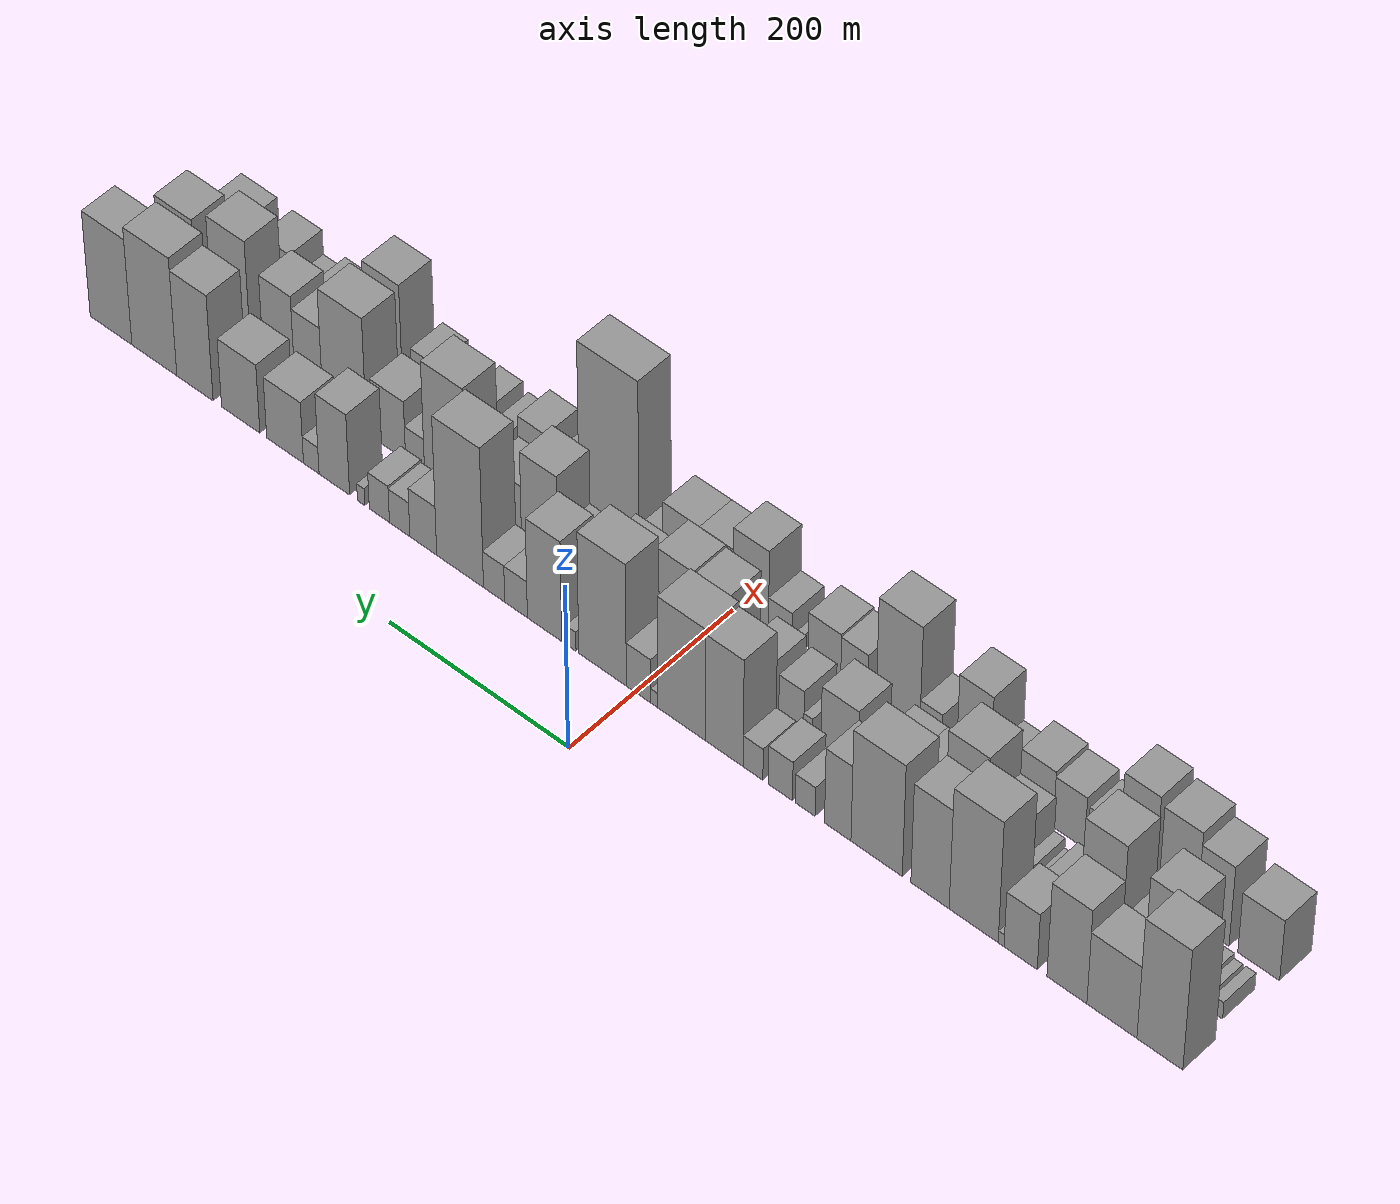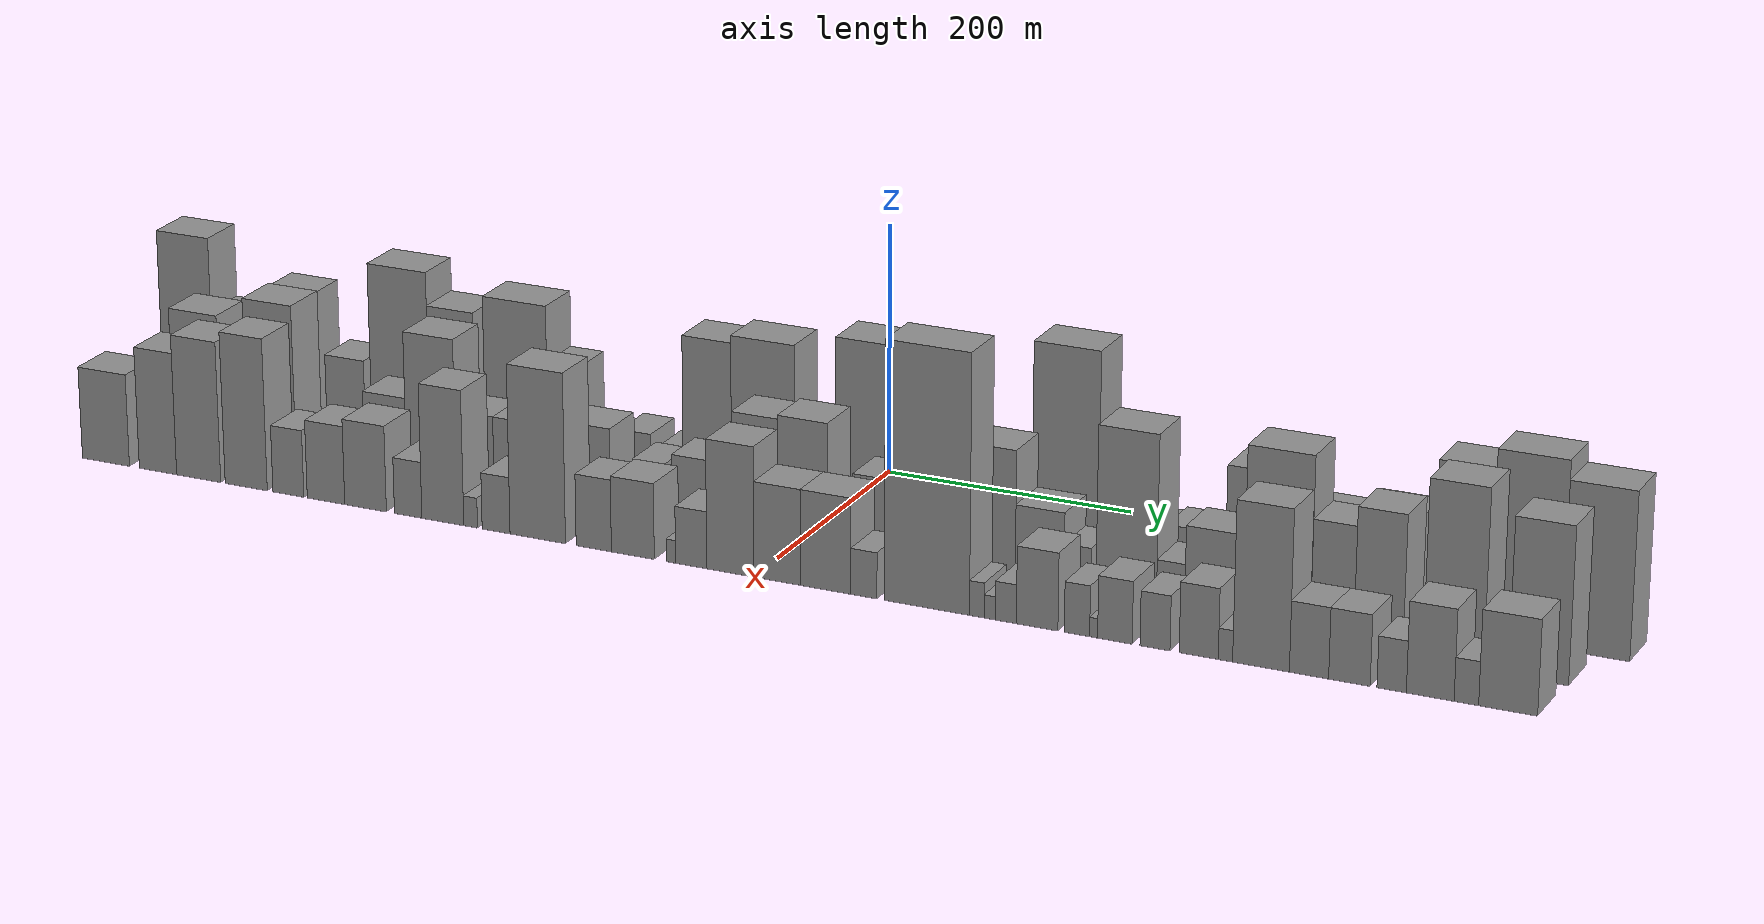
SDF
<sdf version="1.6">
 <world name="default">
  <scene>
   <sky><clouds><speed>12</speed></clouds></sky>
   <ambient>0.4 0.4 0.4 1</ambient>
   <background>0.7 0.7 0.7 1</background>
   <shadows>1</shadows>
  </scene>
  <gravity>0 0 -9.8066</gravity>
  <magnetic_field>6e-06 2.3e-05 -4.2e-05</magnetic_field>
  <physics default="0" name="default_physics" type="ode">
   <ode>
    <solver>
     <type>quick</type>
     <iters>10</iters>
     <sor>1.0</sor>
     <use_dynamic_moi_rescaling>0</use_dynamic_moi_rescaling>
    </solver>
    <constraints>
     <cfm>0</cfm>
     <erp>0.2</erp>
     <contact_max_correcting_vel>100</contact_max_correcting_vel>
     <contact_surface_layer>0.001</contact_surface_layer>
    </constraints>
   </ode>
   <max_step_size>0.004</max_step_size>
   <real_time_factor>1</real_time_factor>
   <real_time_update_rate>250</real_time_update_rate>
  </physics>
  <light name="sun" type="directional">
   <pose>0 0 10 0 0 0</pose>
   <diffuse>0.8 0.8 0.8 1</diffuse>
   <specular>0.2 0.2 0.2 1</specular>
   <attenuation>
    <range>1000</range>
    <constant>0.9</constant>
    <linear>0.01</linear>
    <quadratic>0.001</quadratic>
   </attenuation>
   <direction>-0.5 0.1 -0.9</direction>
  </light>
  <model name="building_1">
   <static>1</static>
   <pose>100.0000 -556.6057 0 0.000000 0.000000 0.000000</pose>
   <link name="link">
    <pose>0 0 75.00 0 0 0</pose>
    <collision name="collision"><geometry><box><size>40.0000 46.7887 150.0000</size></box></geometry></collision>
    <visual name="visual">
     <cast_shadows>0</cast_shadows>
     <geometry><box><size>40.0000 46.7887 150.0000</size></box></geometry>
     <material>
      <script>
       <uri>model://grey_wall/materials/scripts</uri>
       <uri>model://grey_wall/materials/textures</uri>
       <name>vrc/grey_wall</name>
      </script>
     </material>
    </visual>
   </link>
  </model>
  <model name="building_2">
   <static>1</static>
   <pose>100.0000 -507.5364 0 0.000000 0.000000 0.000000</pose>
   <link name="link">
    <pose>0 0 45.00 0 0 0</pose>
    <collision name="collision"><geometry><box><size>40.0000 51.3499 90.0000</size></box></geometry></collision>
    <visual name="visual">
     <cast_shadows>0</cast_shadows>
     <geometry><box><size>40.0000 51.3499 90.0000</size></box></geometry>
     <material>
      <script>
       <uri>model://grey_wall/materials/scripts</uri>
       <uri>model://grey_wall/materials/textures</uri>
       <name>vrc/grey_wall</name>
      </script>
     </material>
    </visual>
   </link>
  </model>
  <model name="building_3">
   <static>1</static>
   <pose>100.0000 -461.2235 0 0.000000 0.000000 0.000000</pose>
   <link name="link">
    <pose>0 0 58.50 0 0 0</pose>
    <collision name="collision"><geometry><box><size>40.0000 41.2757 117.0000</size></box></geometry></collision>
    <visual name="visual">
     <cast_shadows>0</cast_shadows>
     <geometry><box><size>40.0000 41.2757 117.0000</size></box></geometry>
     <material>
      <script>
       <uri>model://grey_wall/materials/scripts</uri>
       <uri>model://grey_wall/materials/textures</uri>
       <name>vrc/grey_wall</name>
      </script>
     </material>
    </visual>
   </link>
  </model>
  <model name="building_4">
   <static>1</static>
   <pose>100.0000 -413.2775 0 0.000000 0.000000 0.000000</pose>
   <link name="link">
    <pose>0 0 34.50 0 0 0</pose>
    <collision name="collision"><geometry><box><size>40.0000 34.6164 69.0000</size></box></geometry></collision>
    <visual name="visual">
     <cast_shadows>0</cast_shadows>
     <geometry><box><size>40.0000 34.6164 69.0000</size></box></geometry>
     <material>
      <script>
       <uri>model://grey_wall/materials/scripts</uri>
       <uri>model://grey_wall/materials/textures</uri>
       <name>vrc/grey_wall</name>
      </script>
     </material>
    </visual>
   </link>
  </model>
  <model name="building_5">
   <static>1</static>
   <pose>100.0000 -392.9326 0 0.000000 0.000000 0.000000</pose>
   <link name="link">
    <pose>0 0 7.50 0 0 0</pose>
    <collision name="collision"><geometry><box><size>40.0000 6.0733 15.0000</size></box></geometry></collision>
    <visual name="visual">
     <cast_shadows>0</cast_shadows>
     <geometry><box><size>40.0000 6.0733 15.0000</size></box></geometry>
     <material>
      <script>
       <uri>model://grey_wall/materials/scripts</uri>
       <uri>model://grey_wall/materials/textures</uri>
       <name>vrc/grey_wall</name>
      </script>
     </material>
    </visual>
   </link>
  </model>
  <model name="building_6">
   <static>1</static>
   <pose>100.0000 -364.1682 0 0.000000 0.000000 0.000000</pose>
   <link name="link">
    <pose>0 0 75.00 0 0 0</pose>
    <collision name="collision"><geometry><box><size>40.0000 51.4556 150.0000</size></box></geometry></collision>
    <visual name="visual">
     <cast_shadows>0</cast_shadows>
     <geometry><box><size>40.0000 51.4556 150.0000</size></box></geometry>
     <material>
      <script>
       <uri>model://grey_wall/materials/scripts</uri>
       <uri>model://grey_wall/materials/textures</uri>
       <name>vrc/grey_wall</name>
      </script>
     </material>
    </visual>
   </link>
  </model>
  <model name="building_7">
   <static>1</static>
   <pose>100.0000 -318.2402 0 0.000000 0.000000 0.000000</pose>
   <link name="link">
    <pose>0 0 61.50 0 0 0</pose>
    <collision name="collision"><geometry><box><size>40.0000 40.4003 123.0000</size></box></geometry></collision>
    <visual name="visual">
     <cast_shadows>0</cast_shadows>
     <geometry><box><size>40.0000 40.4003 123.0000</size></box></geometry>
     <material>
      <script>
       <uri>model://grey_wall/materials/scripts</uri>
       <uri>model://grey_wall/materials/textures</uri>
       <name>vrc/grey_wall</name>
      </script>
     </material>
    </visual>
   </link>
  </model>
  <model name="building_8">
   <static>1</static>
   <pose>100.0000 -261.7073 0 0.000000 0.000000 0.000000</pose>
   <link name="link">
    <pose>0 0 69.00 0 0 0</pose>
    <collision name="collision"><geometry><box><size>40.0000 54.6654 138.0000</size></box></geometry></collision>
    <visual name="visual">
     <cast_shadows>0</cast_shadows>
     <geometry><box><size>40.0000 54.6654 138.0000</size></box></geometry>
     <material>
      <script>
       <uri>model://grey_wall/materials/scripts</uri>
       <uri>model://grey_wall/materials/textures</uri>
       <name>vrc/grey_wall</name>
      </script>
     </material>
    </visual>
   </link>
  </model>
  <model name="building_9">
   <static>1</static>
   <pose>100.0000 -220.2208 0 0.000000 0.000000 0.000000</pose>
   <link name="link">
    <pose>0 0 46.50 0 0 0</pose>
    <collision name="collision"><geometry><box><size>40.0000 28.3076 93.0000</size></box></geometry></collision>
    <visual name="visual">
     <cast_shadows>0</cast_shadows>
     <geometry><box><size>40.0000 28.3076 93.0000</size></box></geometry>
     <material>
      <script>
       <uri>model://grey_wall/materials/scripts</uri>
       <uri>model://grey_wall/materials/textures</uri>
       <name>vrc/grey_wall</name>
      </script>
     </material>
    </visual>
   </link>
  </model>
  <model name="building_10">
   <static>1</static>
   <pose>100.0000 -185.3479 0 0.000000 0.000000 0.000000</pose>
   <link name="link">
    <pose>0 0 18.00 0 0 0</pose>
    <collision name="collision"><geometry><box><size>40.0000 21.4381 36.0000</size></box></geometry></collision>
    <visual name="visual">
     <cast_shadows>0</cast_shadows>
     <geometry><box><size>40.0000 21.4381 36.0000</size></box></geometry>
     <material>
      <script>
       <uri>model://grey_wall/materials/scripts</uri>
       <uri>model://grey_wall/materials/textures</uri>
       <name>vrc/grey_wall</name>
      </script>
     </material>
    </visual>
   </link>
  </model>
  <model name="building_11">
   <static>1</static>
   <pose>100.0000 -158.6383 0 0.000000 0.000000 0.000000</pose>
   <link name="link">
    <pose>0 0 24.00 0 0 0</pose>
    <collision name="collision"><geometry><box><size>40.0000 25.9812 48.0000</size></box></geometry></collision>
    <visual name="visual">
     <cast_shadows>0</cast_shadows>
     <geometry><box><size>40.0000 25.9812 48.0000</size></box></geometry>
     <material>
      <script>
       <uri>model://grey_wall/materials/scripts</uri>
       <uri>model://grey_wall/materials/textures</uri>
       <name>vrc/grey_wall</name>
      </script>
     </material>
    </visual>
   </link>
  </model>
  <model name="building_12">
   <static>1</static>
   <pose>100.0000 -128.9441 0 0.000000 0.000000 0.000000</pose>
   <link name="link">
    <pose>0 0 19.50 0 0 0</pose>
    <collision name="collision"><geometry><box><size>40.0000 21.4073 39.0000</size></box></geometry></collision>
    <visual name="visual">
     <cast_shadows>0</cast_shadows>
     <geometry><box><size>40.0000 21.4073 39.0000</size></box></geometry>
     <material>
      <script>
       <uri>model://grey_wall/materials/scripts</uri>
       <uri>model://grey_wall/materials/textures</uri>
       <name>vrc/grey_wall</name>
      </script>
     </material>
    </visual>
   </link>
  </model>
  <model name="building_13">
   <static>1</static>
   <pose>100.0000 -97.7758 0 0.000000 0.000000 0.000000</pose>
   <link name="link">
    <pose>0 0 66.00 0 0 0</pose>
    <collision name="collision"><geometry><box><size>40.0000 40.9294 132.0000</size></box></geometry></collision>
    <visual name="visual">
     <cast_shadows>0</cast_shadows>
     <geometry><box><size>40.0000 40.9294 132.0000</size></box></geometry>
     <material>
      <script>
       <uri>model://grey_wall/materials/scripts</uri>
       <uri>model://grey_wall/materials/textures</uri>
       <name>vrc/grey_wall</name>
      </script>
     </material>
    </visual>
   </link>
  </model>
  <model name="building_14">
   <static>1</static>
   <pose>100.0000 -50.9535 0 0.000000 0.000000 0.000000</pose>
   <link name="link">
    <pose>0 0 69.00 0 0 0</pose>
    <collision name="collision"><geometry><box><size>40.0000 52.7151 138.0000</size></box></geometry></collision>
    <visual name="visual">
     <cast_shadows>0</cast_shadows>
     <geometry><box><size>40.0000 52.7151 138.0000</size></box></geometry>
     <material>
      <script>
       <uri>model://grey_wall/materials/scripts</uri>
       <uri>model://grey_wall/materials/textures</uri>
       <name>vrc/grey_wall</name>
      </script>
     </material>
    </visual>
   </link>
  </model>
  <model name="building_15">
   <static>1</static>
   <pose>100.0000 -20.9547 0 0.000000 0.000000 0.000000</pose>
   <link name="link">
    <pose>0 0 9.00 0 0 0</pose>
    <collision name="collision"><geometry><box><size>40.0000 7.2826 18.0000</size></box></geometry></collision>
    <visual name="visual">
     <cast_shadows>0</cast_shadows>
     <geometry><box><size>40.0000 7.2826 18.0000</size></box></geometry>
     <material>
      <script>
       <uri>model://grey_wall/materials/scripts</uri>
       <uri>model://grey_wall/materials/textures</uri>
       <name>vrc/grey_wall</name>
      </script>
     </material>
    </visual>
   </link>
  </model>
  <model name="building_16">
   <static>1</static>
   <pose>100.0000 -3.7661 0 0.000000 0.000000 0.000000</pose>
   <link name="link">
    <pose>0 0 27.00 0 0 0</pose>
    <collision name="collision"><geometry><box><size>40.0000 27.0945 54.0000</size></box></geometry></collision>
    <visual name="visual">
     <cast_shadows>0</cast_shadows>
     <geometry><box><size>40.0000 27.0945 54.0000</size></box></geometry>
     <material>
      <script>
       <uri>model://grey_wall/materials/scripts</uri>
       <uri>model://grey_wall/materials/textures</uri>
       <name>vrc/grey_wall</name>
      </script>
     </material>
    </visual>
   </link>
  </model>
  <model name="building_17">
   <static>1</static>
   <pose>100.0000 36.2147 0 0.000000 0.000000 0.000000</pose>
   <link name="link">
    <pose>0 0 75.00 0 0 0</pose>
    <collision name="collision"><geometry><box><size>40.0000 52.8672 150.0000</size></box></geometry></collision>
    <visual name="visual">
     <cast_shadows>0</cast_shadows>
     <geometry><box><size>40.0000 52.8672 150.0000</size></box></geometry>
     <material>
      <script>
       <uri>model://grey_wall/materials/scripts</uri>
       <uri>model://grey_wall/materials/textures</uri>
       <name>vrc/grey_wall</name>
      </script>
     </material>
    </visual>
   </link>
  </model>
  <model name="building_18">
   <static>1</static>
   <pose>100.0000 71.1362 0 0.000000 0.000000 0.000000</pose>
   <link name="link">
    <pose>0 0 12.00 0 0 0</pose>
    <collision name="collision"><geometry><box><size>40.0000 10.9758 24.0000</size></box></geometry></collision>
    <visual name="visual">
     <cast_shadows>0</cast_shadows>
     <geometry><box><size>40.0000 10.9758 24.0000</size></box></geometry>
     <material>
      <script>
       <uri>model://grey_wall/materials/scripts</uri>
       <uri>model://grey_wall/materials/textures</uri>
       <name>vrc/grey_wall</name>
      </script>
     </material>
    </visual>
   </link>
  </model>
  <model name="building_19">
   <static>1</static>
   <pose>100.0000 100.8529 0 0.000000 0.000000 0.000000</pose>
   <link name="link">
    <pose>0 0 61.50 0 0 0</pose>
    <collision name="collision"><geometry><box><size>40.0000 38.4576 123.0000</size></box></geometry></collision>
    <visual name="visual">
     <cast_shadows>0</cast_shadows>
     <geometry><box><size>40.0000 38.4576 123.0000</size></box></geometry>
     <material>
      <script>
       <uri>model://grey_wall/materials/scripts</uri>
       <uri>model://grey_wall/materials/textures</uri>
       <name>vrc/grey_wall</name>
      </script>
     </material>
    </visual>
   </link>
  </model>
  <model name="building_20">
   <static>1</static>
   <pose>100.0000 132.8701 0 0.000000 0.000000 0.000000</pose>
   <link name="link">
    <pose>0 0 22.50 0 0 0</pose>
    <collision name="collision"><geometry><box><size>40.0000 25.5769 45.0000</size></box></geometry></collision>
    <visual name="visual">
     <cast_shadows>0</cast_shadows>
     <geometry><box><size>40.0000 25.5769 45.0000</size></box></geometry>
     <material>
      <script>
       <uri>model://grey_wall/materials/scripts</uri>
       <uri>model://grey_wall/materials/textures</uri>
       <name>vrc/grey_wall</name>
      </script>
     </material>
    </visual>
   </link>
  </model>
  <model name="building_21">
   <static>1</static>
   <pose>100.0000 157.6431 0 0.000000 0.000000 0.000000</pose>
   <link name="link">
    <pose>0 0 22.50 0 0 0</pose>
    <collision name="collision"><geometry><box><size>40.0000 23.9690 45.0000</size></box></geometry></collision>
    <visual name="visual">
     <cast_shadows>0</cast_shadows>
     <geometry><box><size>40.0000 23.9690 45.0000</size></box></geometry>
     <material>
      <script>
       <uri>model://grey_wall/materials/scripts</uri>
       <uri>model://grey_wall/materials/textures</uri>
       <name>vrc/grey_wall</name>
      </script>
     </material>
    </visual>
   </link>
  </model>
  <model name="building_22">
   <static>1</static>
   <pose>100.0000 196.2056 0 0.000000 0.000000 0.000000</pose>
   <link name="link">
    <pose>0 0 85.50 0 0 0</pose>
    <collision name="collision"><geometry><box><size>40.0000 53.1561 171.0000</size></box></geometry></collision>
    <visual name="visual">
     <cast_shadows>0</cast_shadows>
     <geometry><box><size>40.0000 53.1561 171.0000</size></box></geometry>
     <material>
      <script>
       <uri>model://grey_wall/materials/scripts</uri>
       <uri>model://grey_wall/materials/textures</uri>
       <name>vrc/grey_wall</name>
      </script>
     </material>
    </visual>
   </link>
  </model>
  <model name="building_23">
   <static>1</static>
   <pose>100.0000 238.1051 0 0.000000 0.000000 0.000000</pose>
   <link name="link">
    <pose>0 0 30.00 0 0 0</pose>
    <collision name="collision"><geometry><box><size>40.0000 30.6430 60.0000</size></box></geometry></collision>
    <visual name="visual">
     <cast_shadows>0</cast_shadows>
     <geometry><box><size>40.0000 30.6430 60.0000</size></box></geometry>
     <material>
      <script>
       <uri>model://grey_wall/materials/scripts</uri>
       <uri>model://grey_wall/materials/textures</uri>
       <name>vrc/grey_wall</name>
      </script>
     </material>
    </visual>
   </link>
  </model>
  <model name="building_24">
   <static>1</static>
   <pose>100.0000 265.1412 0 0.000000 0.000000 0.000000</pose>
   <link name="link">
    <pose>0 0 21.00 0 0 0</pose>
    <collision name="collision"><geometry><box><size>40.0000 23.4290 42.0000</size></box></geometry></collision>
    <visual name="visual">
     <cast_shadows>0</cast_shadows>
     <geometry><box><size>40.0000 23.4290 42.0000</size></box></geometry>
     <material>
      <script>
       <uri>model://grey_wall/materials/scripts</uri>
       <uri>model://grey_wall/materials/textures</uri>
       <name>vrc/grey_wall</name>
      </script>
     </material>
    </visual>
   </link>
  </model>
  <model name="building_25">
   <static>1</static>
   <pose>100.0000 288.4493 0 0.000000 0.000000 0.000000</pose>
   <link name="link">
    <pose>0 0 22.50 0 0 0</pose>
    <collision name="collision"><geometry><box><size>40.0000 23.1873 45.0000</size></box></geometry></collision>
    <visual name="visual">
     <cast_shadows>0</cast_shadows>
     <geometry><box><size>40.0000 23.1873 45.0000</size></box></geometry>
     <material>
      <script>
       <uri>model://grey_wall/materials/scripts</uri>
       <uri>model://grey_wall/materials/textures</uri>
       <name>vrc/grey_wall</name>
      </script>
     </material>
    </visual>
   </link>
  </model>
  <model name="building_26">
   <static>1</static>
   <pose>100.0000 309.3964 0 0.000000 0.000000 0.000000</pose>
   <link name="link">
    <pose>0 0 10.50 0 0 0</pose>
    <collision name="collision"><geometry><box><size>40.0000 8.7069 21.0000</size></box></geometry></collision>
    <visual name="visual">
     <cast_shadows>0</cast_shadows>
     <geometry><box><size>40.0000 8.7069 21.0000</size></box></geometry>
     <material>
      <script>
       <uri>model://grey_wall/materials/scripts</uri>
       <uri>model://grey_wall/materials/textures</uri>
       <name>vrc/grey_wall</name>
      </script>
     </material>
    </visual>
   </link>
  </model>
  <model name="building_27">
   <static>1</static>
   <pose>100.0000 340.4459 0 0.000000 0.000000 0.000000</pose>
   <link name="link">
    <pose>0 0 49.50 0 0 0</pose>
    <collision name="collision"><geometry><box><size>40.0000 35.3920 99.0000</size></box></geometry></collision>
    <visual name="visual">
     <cast_shadows>0</cast_shadows>
     <geometry><box><size>40.0000 35.3920 99.0000</size></box></geometry>
     <material>
      <script>
       <uri>model://grey_wall/materials/scripts</uri>
       <uri>model://grey_wall/materials/textures</uri>
       <name>vrc/grey_wall</name>
      </script>
     </material>
    </visual>
   </link>
  </model>
  <model name="building_28">
   <static>1</static>
   <pose>100.0000 367.2024 0 0.000000 0.000000 0.000000</pose>
   <link name="link">
    <pose>0 0 16.50 0 0 0</pose>
    <collision name="collision"><geometry><box><size>40.0000 18.1211 33.0000</size></box></geometry></collision>
    <visual name="visual">
     <cast_shadows>0</cast_shadows>
     <geometry><box><size>40.0000 18.1211 33.0000</size></box></geometry>
     <material>
      <script>
       <uri>model://grey_wall/materials/scripts</uri>
       <uri>model://grey_wall/materials/textures</uri>
       <name>vrc/grey_wall</name>
      </script>
     </material>
    </visual>
   </link>
  </model>
  <model name="building_29">
   <static>1</static>
   <pose>100.0000 397.7496 0 0.000000 0.000000 0.000000</pose>
   <link name="link">
    <pose>0 0 37.50 0 0 0</pose>
    <collision name="collision"><geometry><box><size>40.0000 42.9734 75.0000</size></box></geometry></collision>
    <visual name="visual">
     <cast_shadows>0</cast_shadows>
     <geometry><box><size>40.0000 42.9734 75.0000</size></box></geometry>
     <material>
      <script>
       <uri>model://grey_wall/materials/scripts</uri>
       <uri>model://grey_wall/materials/textures</uri>
       <name>vrc/grey_wall</name>
      </script>
     </material>
    </visual>
   </link>
  </model>
  <model name="building_30">
   <static>1</static>
   <pose>100.0000 449.7620 0 0.000000 0.000000 0.000000</pose>
   <link name="link">
    <pose>0 0 42.00 0 0 0</pose>
    <collision name="collision"><geometry><box><size>40.0000 45.0514 84.0000</size></box></geometry></collision>
    <visual name="visual">
     <cast_shadows>0</cast_shadows>
     <geometry><box><size>40.0000 45.0514 84.0000</size></box></geometry>
     <material>
      <script>
       <uri>model://grey_wall/materials/scripts</uri>
       <uri>model://grey_wall/materials/textures</uri>
       <name>vrc/grey_wall</name>
      </script>
     </material>
    </visual>
   </link>
  </model>
  <model name="building_31">
   <static>1</static>
   <pose>100.0000 503.7873 0 0.000000 0.000000 0.000000</pose>
   <link name="link">
    <pose>0 0 64.50 0 0 0</pose>
    <collision name="collision"><geometry><box><size>40.0000 42.9991 129.0000</size></box></geometry></collision>
    <visual name="visual">
     <cast_shadows>0</cast_shadows>
     <geometry><box><size>40.0000 42.9991 129.0000</size></box></geometry>
     <material>
      <script>
       <uri>model://grey_wall/materials/scripts</uri>
       <uri>model://grey_wall/materials/textures</uri>
       <name>vrc/grey_wall</name>
      </script>
     </material>
    </visual>
   </link>
  </model>
  <model name="building_32">
   <static>1</static>
   <pose>100.0000 552.1299 0 0.000000 0.000000 0.000000</pose>
   <link name="link">
    <pose>0 0 72.00 0 0 0</pose>
    <collision name="collision"><geometry><box><size>40.0000 53.6861 144.0000</size></box></geometry></collision>
    <visual name="visual">
     <cast_shadows>0</cast_shadows>
     <geometry><box><size>40.0000 53.6861 144.0000</size></box></geometry>
     <material>
      <script>
       <uri>model://grey_wall/materials/scripts</uri>
       <uri>model://grey_wall/materials/textures</uri>
       <name>vrc/grey_wall</name>
      </script>
     </material>
    </visual>
   </link>
  </model>
  <model name="building_33">
   <static>1</static>
   <pose>100.0000 603.9876 0 0.000000 0.000000 0.000000</pose>
   <link name="link">
    <pose>0 0 64.50 0 0 0</pose>
    <collision name="collision"><geometry><box><size>40.0000 50.0294 129.0000</size></box></geometry></collision>
    <visual name="visual">
     <cast_shadows>0</cast_shadows>
     <geometry><box><size>40.0000 50.0294 129.0000</size></box></geometry>
     <material>
      <script>
       <uri>model://grey_wall/materials/scripts</uri>
       <uri>model://grey_wall/materials/textures</uri>
       <name>vrc/grey_wall</name>
      </script>
     </material>
    </visual>
   </link>
  </model>
  <model name="building_34">
   <static>1</static>
   <pose>160.0000 -565.9873 0 0.000000 0.000000 0.000000</pose>
   <link name="link">
    <pose>0 0 10.50 0 0 0</pose>
    <collision name="collision"><geometry><box><size>40.0000 10.0253 21.0000</size></box></geometry></collision>
    <visual name="visual">
     <cast_shadows>0</cast_shadows>
     <geometry><box><size>40.0000 10.0253 21.0000</size></box></geometry>
     <material>
      <script>
       <uri>model://grey_wall/materials/scripts</uri>
       <uri>model://grey_wall/materials/textures</uri>
       <name>vrc/grey_wall</name>
      </script>
     </material>
    </visual>
   </link>
  </model>
  <model name="building_35">
   <static>1</static>
   <pose>160.0000 -553.3442 0 0.000000 0.000000 0.000000</pose>
   <link name="link">
    <pose>0 0 10.50 0 0 0</pose>
    <collision name="collision"><geometry><box><size>40.0000 9.2609 21.0000</size></box></geometry></collision>
    <visual name="visual">
     <cast_shadows>0</cast_shadows>
     <geometry><box><size>40.0000 9.2609 21.0000</size></box></geometry>
     <material>
      <script>
       <uri>model://grey_wall/materials/scripts</uri>
       <uri>model://grey_wall/materials/textures</uri>
       <name>vrc/grey_wall</name>
      </script>
     </material>
    </visual>
   </link>
  </model>
  <model name="building_36">
   <static>1</static>
   <pose>160.0000 -542.7825 0 0.000000 0.000000 0.000000</pose>
   <link name="link">
    <pose>0 0 13.50 0 0 0</pose>
    <collision name="collision"><geometry><box><size>40.0000 11.8624 27.0000</size></box></geometry></collision>
    <visual name="visual">
     <cast_shadows>0</cast_shadows>
     <geometry><box><size>40.0000 11.8624 27.0000</size></box></geometry>
     <material>
      <script>
       <uri>model://grey_wall/materials/scripts</uri>
       <uri>model://grey_wall/materials/textures</uri>
       <name>vrc/grey_wall</name>
      </script>
     </material>
    </visual>
   </link>
  </model>
  <model name="building_37">
   <static>1</static>
   <pose>160.0000 -512.3643 0 0.000000 0.000000 0.000000</pose>
   <link name="link">
    <pose>0 0 55.50 0 0 0</pose>
    <collision name="collision"><geometry><box><size>40.0000 42.9741 111.0000</size></box></geometry></collision>
    <visual name="visual">
     <cast_shadows>0</cast_shadows>
     <geometry><box><size>40.0000 42.9741 111.0000</size></box></geometry>
     <material>
      <script>
       <uri>model://grey_wall/materials/scripts</uri>
       <uri>model://grey_wall/materials/textures</uri>
       <name>vrc/grey_wall</name>
      </script>
     </material>
    </visual>
   </link>
  </model>
  <model name="building_38">
   <static>1</static>
   <pose>160.0000 -478.8510 0 0.000000 0.000000 0.000000</pose>
   <link name="link">
    <pose>0 0 21.00 0 0 0</pose>
    <collision name="collision"><geometry><box><size>40.0000 24.0523 42.0000</size></box></geometry></collision>
    <visual name="visual">
     <cast_shadows>0</cast_shadows>
     <geometry><box><size>40.0000 24.0523 42.0000</size></box></geometry>
     <material>
      <script>
       <uri>model://grey_wall/materials/scripts</uri>
       <uri>model://grey_wall/materials/textures</uri>
       <name>vrc/grey_wall</name>
      </script>
     </material>
    </visual>
   </link>
  </model>
  <model name="building_39">
   <static>1</static>
   <pose>160.0000 -445.1828 0 0.000000 0.000000 0.000000</pose>
   <link name="link">
    <pose>0 0 64.50 0 0 0</pose>
    <collision name="collision"><geometry><box><size>40.0000 43.2841 129.0000</size></box></geometry></collision>
    <visual name="visual">
     <cast_shadows>0</cast_shadows>
     <geometry><box><size>40.0000 43.2841 129.0000</size></box></geometry>
     <material>
      <script>
       <uri>model://grey_wall/materials/scripts</uri>
       <uri>model://grey_wall/materials/textures</uri>
       <name>vrc/grey_wall</name>
      </script>
     </material>
    </visual>
   </link>
  </model>
  <model name="building_40">
   <static>1</static>
   <pose>160.0000 -415.0381 0 0.000000 0.000000 0.000000</pose>
   <link name="link">
    <pose>0 0 15.00 0 0 0</pose>
    <collision name="collision"><geometry><box><size>40.0000 17.0053 30.0000</size></box></geometry></collision>
    <visual name="visual">
     <cast_shadows>0</cast_shadows>
     <geometry><box><size>40.0000 17.0053 30.0000</size></box></geometry>
     <material>
      <script>
       <uri>model://grey_wall/materials/scripts</uri>
       <uri>model://grey_wall/materials/textures</uri>
       <name>vrc/grey_wall</name>
      </script>
     </material>
    </visual>
   </link>
  </model>
  <model name="building_41">
   <static>1</static>
   <pose>160.0000 -396.8979 0 0.000000 0.000000 0.000000</pose>
   <link name="link">
    <pose>0 0 16.50 0 0 0</pose>
    <collision name="collision"><geometry><box><size>40.0000 19.2752 33.0000</size></box></geometry></collision>
    <visual name="visual">
     <cast_shadows>0</cast_shadows>
     <geometry><box><size>40.0000 19.2752 33.0000</size></box></geometry>
     <material>
      <script>
       <uri>model://grey_wall/materials/scripts</uri>
       <uri>model://grey_wall/materials/textures</uri>
       <name>vrc/grey_wall</name>
      </script>
     </material>
    </visual>
   </link>
  </model>
  <model name="building_42">
   <static>1</static>
   <pose>160.0000 -377.6748 0 0.000000 0.000000 0.000000</pose>
   <link name="link">
    <pose>0 0 7.50 0 0 0</pose>
    <collision name="collision"><geometry><box><size>40.0000 7.1710 15.0000</size></box></geometry></collision>
    <visual name="visual">
     <cast_shadows>0</cast_shadows>
     <geometry><box><size>40.0000 7.1710 15.0000</size></box></geometry>
     <material>
      <script>
       <uri>model://grey_wall/materials/scripts</uri>
       <uri>model://grey_wall/materials/textures</uri>
       <name>vrc/grey_wall</name>
      </script>
     </material>
    </visual>
   </link>
  </model>
  <model name="building_43">
   <static>1</static>
   <pose>160.0000 -368.3267 0 0.000000 0.000000 0.000000</pose>
   <link name="link">
    <pose>0 0 13.50 0 0 0</pose>
    <collision name="collision"><geometry><box><size>40.0000 11.5252 27.0000</size></box></geometry></collision>
    <visual name="visual">
     <cast_shadows>0</cast_shadows>
     <geometry><box><size>40.0000 11.5252 27.0000</size></box></geometry>
     <material>
      <script>
       <uri>model://grey_wall/materials/scripts</uri>
       <uri>model://grey_wall/materials/textures</uri>
       <name>vrc/grey_wall</name>
      </script>
     </material>
    </visual>
   </link>
  </model>
  <model name="building_44">
   <static>1</static>
   <pose>160.0000 -343.9430 0 0.000000 0.000000 0.000000</pose>
   <link name="link">
    <pose>0 0 34.50 0 0 0</pose>
    <collision name="collision"><geometry><box><size>40.0000 37.2422 69.0000</size></box></geometry></collision>
    <visual name="visual">
     <cast_shadows>0</cast_shadows>
     <geometry><box><size>40.0000 37.2422 69.0000</size></box></geometry>
     <material>
      <script>
       <uri>model://grey_wall/materials/scripts</uri>
       <uri>model://grey_wall/materials/textures</uri>
       <name>vrc/grey_wall</name>
      </script>
     </material>
    </visual>
   </link>
  </model>
  <model name="building_45">
   <static>1</static>
   <pose>160.0000 -303.7609 0 0.000000 0.000000 0.000000</pose>
   <link name="link">
    <pose>0 0 61.50 0 0 0</pose>
    <collision name="collision"><geometry><box><size>40.0000 43.1222 123.0000</size></box></geometry></collision>
    <visual name="visual">
     <cast_shadows>0</cast_shadows>
     <geometry><box><size>40.0000 43.1222 123.0000</size></box></geometry>
     <material>
      <script>
       <uri>model://grey_wall/materials/scripts</uri>
       <uri>model://grey_wall/materials/textures</uri>
       <name>vrc/grey_wall</name>
      </script>
     </material>
    </visual>
   </link>
  </model>
  <model name="building_46">
   <static>1</static>
   <pose>160.0000 -265.6744 0 0.000000 0.000000 0.000000</pose>
   <link name="link">
    <pose>0 0 33.00 0 0 0</pose>
    <collision name="collision"><geometry><box><size>40.0000 33.0507 66.0000</size></box></geometry></collision>
    <visual name="visual">
     <cast_shadows>0</cast_shadows>
     <geometry><box><size>40.0000 33.0507 66.0000</size></box></geometry>
     <material>
      <script>
       <uri>model://grey_wall/materials/scripts</uri>
       <uri>model://grey_wall/materials/textures</uri>
       <name>vrc/grey_wall</name>
      </script>
     </material>
    </visual>
   </link>
  </model>
  <model name="building_47">
   <static>1</static>
   <pose>160.0000 -231.5568 0 0.000000 0.000000 0.000000</pose>
   <link name="link">
    <pose>0 0 33.00 0 0 0</pose>
    <collision name="collision"><geometry><box><size>40.0000 35.1845 66.0000</size></box></geometry></collision>
    <visual name="visual">
     <cast_shadows>0</cast_shadows>
     <geometry><box><size>40.0000 35.1845 66.0000</size></box></geometry>
     <material>
      <script>
       <uri>model://grey_wall/materials/scripts</uri>
       <uri>model://grey_wall/materials/textures</uri>
       <name>vrc/grey_wall</name>
      </script>
     </material>
    </visual>
   </link>
  </model>
  <model name="building_48">
   <static>1</static>
   <pose>160.0000 -204.5643 0 0.000000 0.000000 0.000000</pose>
   <link name="link">
    <pose>0 0 18.00 0 0 0</pose>
    <collision name="collision"><geometry><box><size>40.0000 18.8004 36.0000</size></box></geometry></collision>
    <visual name="visual">
     <cast_shadows>0</cast_shadows>
     <geometry><box><size>40.0000 18.8004 36.0000</size></box></geometry>
     <material>
      <script>
       <uri>model://grey_wall/materials/scripts</uri>
       <uri>model://grey_wall/materials/textures</uri>
       <name>vrc/grey_wall</name>
      </script>
     </material>
    </visual>
   </link>
  </model>
  <model name="building_49">
   <static>1</static>
   <pose>160.0000 -169.2522 0 0.000000 0.000000 0.000000</pose>
   <link name="link">
    <pose>0 0 36.00 0 0 0</pose>
    <collision name="collision"><geometry><box><size>40.0000 39.8238 72.0000</size></box></geometry></collision>
    <visual name="visual">
     <cast_shadows>0</cast_shadows>
     <geometry><box><size>40.0000 39.8238 72.0000</size></box></geometry>
     <material>
      <script>
       <uri>model://grey_wall/materials/scripts</uri>
       <uri>model://grey_wall/materials/textures</uri>
       <name>vrc/grey_wall</name>
      </script>
     </material>
    </visual>
   </link>
  </model>
  <model name="building_50">
   <static>1</static>
   <pose>160.0000 -135.4877 0 0.000000 0.000000 0.000000</pose>
   <link name="link">
    <pose>0 0 12.00 0 0 0</pose>
    <collision name="collision"><geometry><box><size>40.0000 9.7053 24.0000</size></box></geometry></collision>
    <visual name="visual">
     <cast_shadows>0</cast_shadows>
     <geometry><box><size>40.0000 9.7053 24.0000</size></box></geometry>
     <material>
      <script>
       <uri>model://grey_wall/materials/scripts</uri>
       <uri>model://grey_wall/materials/textures</uri>
       <name>vrc/grey_wall</name>
      </script>
     </material>
    </visual>
   </link>
  </model>
  <model name="building_51">
   <static>1</static>
   <pose>160.0000 -117.0785 0 0.000000 0.000000 0.000000</pose>
   <link name="link">
    <pose>0 0 25.50 0 0 0</pose>
    <collision name="collision"><geometry><box><size>40.0000 27.1130 51.0000</size></box></geometry></collision>
    <visual name="visual">
     <cast_shadows>0</cast_shadows>
     <geometry><box><size>40.0000 27.1130 51.0000</size></box></geometry>
     <material>
      <script>
       <uri>model://grey_wall/materials/scripts</uri>
       <uri>model://grey_wall/materials/textures</uri>
       <name>vrc/grey_wall</name>
      </script>
     </material>
    </visual>
   </link>
  </model>
  <model name="building_52">
   <static>1</static>
   <pose>160.0000 -81.5995 0 0.000000 0.000000 0.000000</pose>
   <link name="link">
    <pose>0 0 30.00 0 0 0</pose>
    <collision name="collision"><geometry><box><size>40.0000 31.8449 60.0000</size></box></geometry></collision>
    <visual name="visual">
     <cast_shadows>0</cast_shadows>
     <geometry><box><size>40.0000 31.8449 60.0000</size></box></geometry>
     <material>
      <script>
       <uri>model://grey_wall/materials/scripts</uri>
       <uri>model://grey_wall/materials/textures</uri>
       <name>vrc/grey_wall</name>
      </script>
     </material>
    </visual>
   </link>
  </model>
  <model name="building_53">
   <static>1</static>
   <pose>160.0000 -56.6211 0 0.000000 0.000000 0.000000</pose>
   <link name="link">
    <pose>0 0 16.50 0 0 0</pose>
    <collision name="collision"><geometry><box><size>40.0000 18.1120 33.0000</size></box></geometry></collision>
    <visual name="visual">
     <cast_shadows>0</cast_shadows>
     <geometry><box><size>40.0000 18.1120 33.0000</size></box></geometry>
     <material>
      <script>
       <uri>model://grey_wall/materials/scripts</uri>
       <uri>model://grey_wall/materials/textures</uri>
       <name>vrc/grey_wall</name>
      </script>
     </material>
    </visual>
   </link>
  </model>
  <model name="building_54">
   <static>1</static>
   <pose>160.0000 -28.6241 0 0.000000 0.000000 0.000000</pose>
   <link name="link">
    <pose>0 0 51.00 0 0 0</pose>
    <collision name="collision"><geometry><box><size>40.0000 37.8820 102.0000</size></box></geometry></collision>
    <visual name="visual">
     <cast_shadows>0</cast_shadows>
     <geometry><box><size>40.0000 37.8820 102.0000</size></box></geometry>
     <material>
      <script>
       <uri>model://grey_wall/materials/scripts</uri>
       <uri>model://grey_wall/materials/textures</uri>
       <name>vrc/grey_wall</name>
      </script>
     </material>
    </visual>
   </link>
  </model>
  <model name="building_55">
   <static>1</static>
   <pose>160.0000 10.7575 0 0.000000 0.000000 0.000000</pose>
   <link name="link">
    <pose>0 0 52.50 0 0 0</pose>
    <collision name="collision"><geometry><box><size>40.0000 40.8811 105.0000</size></box></geometry></collision>
    <visual name="visual">
     <cast_shadows>0</cast_shadows>
     <geometry><box><size>40.0000 40.8811 105.0000</size></box></geometry>
     <material>
      <script>
       <uri>model://grey_wall/materials/scripts</uri>
       <uri>model://grey_wall/materials/textures</uri>
       <name>vrc/grey_wall</name>
      </script>
     </material>
    </visual>
   </link>
  </model>
  <model name="building_56">
   <static>1</static>
   <pose>160.0000 43.5094 0 0.000000 0.000000 0.000000</pose>
   <link name="link">
    <pose>0 0 16.50 0 0 0</pose>
    <collision name="collision"><geometry><box><size>40.0000 16.6226 33.0000</size></box></geometry></collision>
    <visual name="visual">
     <cast_shadows>0</cast_shadows>
     <geometry><box><size>40.0000 16.6226 33.0000</size></box></geometry>
     <material>
      <script>
       <uri>model://grey_wall/materials/scripts</uri>
       <uri>model://grey_wall/materials/textures</uri>
       <name>vrc/grey_wall</name>
      </script>
     </material>
    </visual>
   </link>
  </model>
  <model name="building_57">
   <static>1</static>
   <pose>160.0000 70.5912 0 0.000000 0.000000 0.000000</pose>
   <link name="link">
    <pose>0 0 34.50 0 0 0</pose>
    <collision name="collision"><geometry><box><size>40.0000 37.5410 69.0000</size></box></geometry></collision>
    <visual name="visual">
     <cast_shadows>0</cast_shadows>
     <geometry><box><size>40.0000 37.5410 69.0000</size></box></geometry>
     <material>
      <script>
       <uri>model://grey_wall/materials/scripts</uri>
       <uri>model://grey_wall/materials/textures</uri>
       <name>vrc/grey_wall</name>
      </script>
     </material>
    </visual>
   </link>
  </model>
  <model name="building_58">
   <static>1</static>
   <pose>160.0000 104.3225 0 0.000000 0.000000 0.000000</pose>
   <link name="link">
    <pose>0 0 28.50 0 0 0</pose>
    <collision name="collision"><geometry><box><size>40.0000 29.9216 57.0000</size></box></geometry></collision>
    <visual name="visual">
     <cast_shadows>0</cast_shadows>
     <geometry><box><size>40.0000 29.9216 57.0000</size></box></geometry>
     <material>
      <script>
       <uri>model://grey_wall/materials/scripts</uri>
       <uri>model://grey_wall/materials/textures</uri>
       <name>vrc/grey_wall</name>
      </script>
     </material>
    </visual>
   </link>
  </model>
  <model name="building_59">
   <static>1</static>
   <pose>160.0000 130.3247 0 0.000000 0.000000 0.000000</pose>
   <link name="link">
    <pose>0 0 21.00 0 0 0</pose>
    <collision name="collision"><geometry><box><size>40.0000 22.0829 42.0000</size></box></geometry></collision>
    <visual name="visual">
     <cast_shadows>0</cast_shadows>
     <geometry><box><size>40.0000 22.0829 42.0000</size></box></geometry>
     <material>
      <script>
       <uri>model://grey_wall/materials/scripts</uri>
       <uri>model://grey_wall/materials/textures</uri>
       <name>vrc/grey_wall</name>
      </script>
     </material>
    </visual>
   </link>
  </model>
  <model name="building_60">
   <static>1</static>
   <pose>160.0000 161.8970 0 0.000000 0.000000 0.000000</pose>
   <link name="link">
    <pose>0 0 54.00 0 0 0</pose>
    <collision name="collision"><geometry><box><size>40.0000 41.0616 108.0000</size></box></geometry></collision>
    <visual name="visual">
     <cast_shadows>0</cast_shadows>
     <geometry><box><size>40.0000 41.0616 108.0000</size></box></geometry>
     <material>
      <script>
       <uri>model://grey_wall/materials/scripts</uri>
       <uri>model://grey_wall/materials/textures</uri>
       <name>vrc/grey_wall</name>
      </script>
     </material>
    </visual>
   </link>
  </model>
  <model name="building_61">
   <static>1</static>
   <pose>160.0000 201.6902 0 0.000000 0.000000 0.000000</pose>
   <link name="link">
    <pose>0 0 33.00 0 0 0</pose>
    <collision name="collision"><geometry><box><size>40.0000 38.5248 66.0000</size></box></geometry></collision>
    <visual name="visual">
     <cast_shadows>0</cast_shadows>
     <geometry><box><size>40.0000 38.5248 66.0000</size></box></geometry>
     <material>
      <script>
       <uri>model://grey_wall/materials/scripts</uri>
       <uri>model://grey_wall/materials/textures</uri>
       <name>vrc/grey_wall</name>
      </script>
     </material>
    </visual>
   </link>
  </model>
  <model name="building_62">
   <static>1</static>
   <pose>160.0000 231.4833 0 0.000000 0.000000 0.000000</pose>
   <link name="link">
    <pose>0 0 21.00 0 0 0</pose>
    <collision name="collision"><geometry><box><size>40.0000 21.0615 42.0000</size></box></geometry></collision>
    <visual name="visual">
     <cast_shadows>0</cast_shadows>
     <geometry><box><size>40.0000 21.0615 42.0000</size></box></geometry>
     <material>
      <script>
       <uri>model://grey_wall/materials/scripts</uri>
       <uri>model://grey_wall/materials/textures</uri>
       <name>vrc/grey_wall</name>
      </script>
     </material>
    </visual>
   </link>
  </model>
  <model name="building_63">
   <static>1</static>
   <pose>160.0000 269.6209 0 0.000000 0.000000 0.000000</pose>
   <link name="link">
    <pose>0 0 69.00 0 0 0</pose>
    <collision name="collision"><geometry><box><size>40.0000 47.2138 138.0000</size></box></geometry></collision>
    <visual name="visual">
     <cast_shadows>0</cast_shadows>
     <geometry><box><size>40.0000 47.2138 138.0000</size></box></geometry>
     <material>
      <script>
       <uri>model://grey_wall/materials/scripts</uri>
       <uri>model://grey_wall/materials/textures</uri>
       <name>vrc/grey_wall</name>
      </script>
     </material>
    </visual>
   </link>
  </model>
  <model name="building_64">
   <static>1</static>
   <pose>160.0000 304.1565 0 0.000000 0.000000 0.000000</pose>
   <link name="link">
    <pose>0 0 21.00 0 0 0</pose>
    <collision name="collision"><geometry><box><size>40.0000 21.8574 42.0000</size></box></geometry></collision>
    <visual name="visual">
     <cast_shadows>0</cast_shadows>
     <geometry><box><size>40.0000 21.8574 42.0000</size></box></geometry>
     <material>
      <script>
       <uri>model://grey_wall/materials/scripts</uri>
       <uri>model://grey_wall/materials/textures</uri>
       <name>vrc/grey_wall</name>
      </script>
     </material>
    </visual>
   </link>
  </model>
  <model name="building_65">
   <static>1</static>
   <pose>160.0000 334.6656 0 0.000000 0.000000 0.000000</pose>
   <link name="link">
    <pose>0 0 36.00 0 0 0</pose>
    <collision name="collision"><geometry><box><size>40.0000 39.1609 72.0000</size></box></geometry></collision>
    <visual name="visual">
     <cast_shadows>0</cast_shadows>
     <geometry><box><size>40.0000 39.1609 72.0000</size></box></geometry>
     <material>
      <script>
       <uri>model://grey_wall/materials/scripts</uri>
       <uri>model://grey_wall/materials/textures</uri>
       <name>vrc/grey_wall</name>
      </script>
     </material>
    </visual>
   </link>
  </model>
  <model name="building_66">
   <static>1</static>
   <pose>160.0000 385.7366 0 0.000000 0.000000 0.000000</pose>
   <link name="link">
    <pose>0 0 70.50 0 0 0</pose>
    <collision name="collision"><geometry><box><size>40.0000 50.9811 141.0000</size></box></geometry></collision>
    <visual name="visual">
     <cast_shadows>0</cast_shadows>
     <geometry><box><size>40.0000 50.9811 141.0000</size></box></geometry>
     <material>
      <script>
       <uri>model://grey_wall/materials/scripts</uri>
       <uri>model://grey_wall/materials/textures</uri>
       <name>vrc/grey_wall</name>
      </script>
     </material>
    </visual>
   </link>
  </model>
  <model name="building_67">
   <static>1</static>
   <pose>160.0000 427.6264 0 0.000000 0.000000 0.000000</pose>
   <link name="link">
    <pose>0 0 46.50 0 0 0</pose>
    <collision name="collision"><geometry><box><size>40.0000 32.7985 93.0000</size></box></geometry></collision>
    <visual name="visual">
     <cast_shadows>0</cast_shadows>
     <geometry><box><size>40.0000 32.7985 93.0000</size></box></geometry>
     <material>
      <script>
       <uri>model://grey_wall/materials/scripts</uri>
       <uri>model://grey_wall/materials/textures</uri>
       <name>vrc/grey_wall</name>
      </script>
     </material>
    </visual>
   </link>
  </model>
  <model name="building_68">
   <static>1</static>
   <pose>160.0000 462.5270 0 0.000000 0.000000 0.000000</pose>
   <link name="link">
    <pose>0 0 54.00 0 0 0</pose>
    <collision name="collision"><geometry><box><size>40.0000 37.0028 108.0000</size></box></geometry></collision>
    <visual name="visual">
     <cast_shadows>0</cast_shadows>
     <geometry><box><size>40.0000 37.0028 108.0000</size></box></geometry>
     <material>
      <script>
       <uri>model://grey_wall/materials/scripts</uri>
       <uri>model://grey_wall/materials/textures</uri>
       <name>vrc/grey_wall</name>
      </script>
     </material>
    </visual>
   </link>
  </model>
  <model name="building_69">
   <static>1</static>
   <pose>160.0000 492.5327 0 0.000000 0.000000 0.000000</pose>
   <link name="link">
    <pose>0 0 7.50 0 0 0</pose>
    <collision name="collision"><geometry><box><size>40.0000 7.0085 15.0000</size></box></geometry></collision>
    <visual name="visual">
     <cast_shadows>0</cast_shadows>
     <geometry><box><size>40.0000 7.0085 15.0000</size></box></geometry>
     <material>
      <script>
       <uri>model://grey_wall/materials/scripts</uri>
       <uri>model://grey_wall/materials/textures</uri>
       <name>vrc/grey_wall</name>
      </script>
     </material>
    </visual>
   </link>
  </model>
  <model name="building_70">
   <static>1</static>
   <pose>160.0000 518.5182 0 0.000000 0.000000 0.000000</pose>
   <link name="link">
    <pose>0 0 69.00 0 0 0</pose>
    <collision name="collision"><geometry><box><size>40.0000 44.9626 138.0000</size></box></geometry></collision>
    <visual name="visual">
     <cast_shadows>0</cast_shadows>
     <geometry><box><size>40.0000 44.9626 138.0000</size></box></geometry>
     <material>
      <script>
       <uri>model://grey_wall/materials/scripts</uri>
       <uri>model://grey_wall/materials/textures</uri>
       <name>vrc/grey_wall</name>
      </script>
     </material>
    </visual>
   </link>
  </model>
  <model name="building_71">
   <static>1</static>
   <pose>160.0000 550.1503 0 0.000000 0.000000 0.000000</pose>
   <link name="link">
    <pose>0 0 16.50 0 0 0</pose>
    <collision name="collision"><geometry><box><size>40.0000 18.3016 33.0000</size></box></geometry></collision>
    <visual name="visual">
     <cast_shadows>0</cast_shadows>
     <geometry><box><size>40.0000 18.3016 33.0000</size></box></geometry>
     <material>
      <script>
       <uri>model://grey_wall/materials/scripts</uri>
       <uri>model://grey_wall/materials/textures</uri>
       <name>vrc/grey_wall</name>
      </script>
     </material>
    </visual>
   </link>
  </model>
  <model name="building_72">
   <static>1</static>
   <pose>160.0000 581.3278 0 0.000000 0.000000 0.000000</pose>
   <link name="link">
    <pose>0 0 60.00 0 0 0</pose>
    <collision name="collision"><geometry><box><size>40.0000 44.0534 120.0000</size></box></geometry></collision>
    <visual name="visual">
     <cast_shadows>0</cast_shadows>
     <geometry><box><size>40.0000 44.0534 120.0000</size></box></geometry>
     <material>
      <script>
       <uri>model://grey_wall/materials/scripts</uri>
       <uri>model://grey_wall/materials/textures</uri>
       <name>vrc/grey_wall</name>
      </script>
     </material>
    </visual>
   </link>
  </model>
  <model name="building_73">
   <static>1</static>
   <pose>220.0000 -558.6510 0 0.000000 0.000000 0.000000</pose>
   <link name="link">
    <pose>0 0 37.50 0 0 0</pose>
    <collision name="collision"><geometry><box><size>40.0000 42.6980 75.0000</size></box></geometry></collision>
    <visual name="visual">
     <cast_shadows>0</cast_shadows>
     <geometry><box><size>40.0000 42.6980 75.0000</size></box></geometry>
     <material>
      <script>
       <uri>model://grey_wall/materials/scripts</uri>
       <uri>model://grey_wall/materials/textures</uri>
       <name>vrc/grey_wall</name>
      </script>
     </material>
    </visual>
   </link>
  </model>
  <model name="building_74">
   <static>1</static>
   <pose>220.0000 -511.4858 0 0.000000 0.000000 0.000000</pose>
   <link name="link">
    <pose>0 0 49.50 0 0 0</pose>
    <collision name="collision"><geometry><box><size>40.0000 33.6324 99.0000</size></box></geometry></collision>
    <visual name="visual">
     <cast_shadows>0</cast_shadows>
     <geometry><box><size>40.0000 33.6324 99.0000</size></box></geometry>
     <material>
      <script>
       <uri>model://grey_wall/materials/scripts</uri>
       <uri>model://grey_wall/materials/textures</uri>
       <name>vrc/grey_wall</name>
      </script>
     </material>
    </visual>
   </link>
  </model>
  <model name="building_75">
   <static>1</static>
   <pose>220.0000 -474.9316 0 0.000000 0.000000 0.000000</pose>
   <link name="link">
    <pose>0 0 57.00 0 0 0</pose>
    <collision name="collision"><geometry><box><size>40.0000 39.4760 114.0000</size></box></geometry></collision>
    <visual name="visual">
     <cast_shadows>0</cast_shadows>
     <geometry><box><size>40.0000 39.4760 114.0000</size></box></geometry>
     <material>
      <script>
       <uri>model://grey_wall/materials/scripts</uri>
       <uri>model://grey_wall/materials/textures</uri>
       <name>vrc/grey_wall</name>
      </script>
     </material>
    </visual>
   </link>
  </model>
  <model name="building_76">
   <static>1</static>
   <pose>220.0000 -432.4911 0 0.000000 0.000000 0.000000</pose>
   <link name="link">
    <pose>0 0 61.50 0 0 0</pose>
    <collision name="collision"><geometry><box><size>40.0000 37.4050 123.0000</size></box></geometry></collision>
    <visual name="visual">
     <cast_shadows>0</cast_shadows>
     <geometry><box><size>40.0000 37.4050 123.0000</size></box></geometry>
     <material>
      <script>
       <uri>model://grey_wall/materials/scripts</uri>
       <uri>model://grey_wall/materials/textures</uri>
       <name>vrc/grey_wall</name>
      </script>
     </material>
    </visual>
   </link>
  </model>
  <model name="building_77">
   <static>1</static>
   <pose>220.0000 -395.1412 0 0.000000 0.000000 0.000000</pose>
   <link name="link">
    <pose>0 0 27.00 0 0 0</pose>
    <collision name="collision"><geometry><box><size>40.0000 27.2949 54.0000</size></box></geometry></collision>
    <visual name="visual">
     <cast_shadows>0</cast_shadows>
     <geometry><box><size>40.0000 27.2949 54.0000</size></box></geometry>
     <material>
      <script>
       <uri>model://grey_wall/materials/scripts</uri>
       <uri>model://grey_wall/materials/textures</uri>
       <name>vrc/grey_wall</name>
      </script>
     </material>
    </visual>
   </link>
  </model>
  <model name="building_78">
   <static>1</static>
   <pose>220.0000 -362.0749 0 0.000000 0.000000 0.000000</pose>
   <link name="link">
    <pose>0 0 31.50 0 0 0</pose>
    <collision name="collision"><geometry><box><size>40.0000 32.8376 63.0000</size></box></geometry></collision>
    <visual name="visual">
     <cast_shadows>0</cast_shadows>
     <geometry><box><size>40.0000 32.8376 63.0000</size></box></geometry>
     <material>
      <script>
       <uri>model://grey_wall/materials/scripts</uri>
       <uri>model://grey_wall/materials/textures</uri>
       <name>vrc/grey_wall</name>
      </script>
     </material>
    </visual>
   </link>
  </model>
  <model name="building_79">
   <static>1</static>
   <pose>220.0000 -327.5263 0 0.000000 0.000000 0.000000</pose>
   <link name="link">
    <pose>0 0 34.50 0 0 0</pose>
    <collision name="collision"><geometry><box><size>40.0000 36.2596 69.0000</size></box></geometry></collision>
    <visual name="visual">
     <cast_shadows>0</cast_shadows>
     <geometry><box><size>40.0000 36.2596 69.0000</size></box></geometry>
     <material>
      <script>
       <uri>model://grey_wall/materials/scripts</uri>
       <uri>model://grey_wall/materials/textures</uri>
       <name>vrc/grey_wall</name>
      </script>
     </material>
    </visual>
   </link>
  </model>
  <model name="building_80">
   <static>1</static>
   <pose>220.0000 -290.5452 0 0.000000 0.000000 0.000000</pose>
   <link name="link">
    <pose>0 0 22.50 0 0 0</pose>
    <collision name="collision"><geometry><box><size>40.0000 23.7028 45.0000</size></box></geometry></collision>
    <visual name="visual">
     <cast_shadows>0</cast_shadows>
     <geometry><box><size>40.0000 23.7028 45.0000</size></box></geometry>
     <material>
      <script>
       <uri>model://grey_wall/materials/scripts</uri>
       <uri>model://grey_wall/materials/textures</uri>
       <name>vrc/grey_wall</name>
      </script>
     </material>
    </visual>
   </link>
  </model>
  <model name="building_81">
   <static>1</static>
   <pose>220.0000 -260.6700 0 0.000000 0.000000 0.000000</pose>
   <link name="link">
    <pose>0 0 54.00 0 0 0</pose>
    <collision name="collision"><geometry><box><size>40.0000 36.0476 108.0000</size></box></geometry></collision>
    <visual name="visual">
     <cast_shadows>0</cast_shadows>
     <geometry><box><size>40.0000 36.0476 108.0000</size></box></geometry>
     <material>
      <script>
       <uri>model://grey_wall/materials/scripts</uri>
       <uri>model://grey_wall/materials/textures</uri>
       <name>vrc/grey_wall</name>
      </script>
     </material>
    </visual>
   </link>
  </model>
  <model name="building_82">
   <static>1</static>
   <pose>220.0000 -236.8047 0 0.000000 0.000000 0.000000</pose>
   <link name="link">
    <pose>0 0 12.00 0 0 0</pose>
    <collision name="collision"><geometry><box><size>40.0000 11.6829 24.0000</size></box></geometry></collision>
    <visual name="visual">
     <cast_shadows>0</cast_shadows>
     <geometry><box><size>40.0000 11.6829 24.0000</size></box></geometry>
     <material>
      <script>
       <uri>model://grey_wall/materials/scripts</uri>
       <uri>model://grey_wall/materials/textures</uri>
       <name>vrc/grey_wall</name>
      </script>
     </material>
    </visual>
   </link>
  </model>
  <model name="building_83">
   <static>1</static>
   <pose>220.0000 -215.0980 0 0.000000 0.000000 0.000000</pose>
   <link name="link">
    <pose>0 0 22.50 0 0 0</pose>
    <collision name="collision"><geometry><box><size>40.0000 23.7305 45.0000</size></box></geometry></collision>
    <visual name="visual">
     <cast_shadows>0</cast_shadows>
     <geometry><box><size>40.0000 23.7305 45.0000</size></box></geometry>
     <material>
      <script>
       <uri>model://grey_wall/materials/scripts</uri>
       <uri>model://grey_wall/materials/textures</uri>
       <name>vrc/grey_wall</name>
      </script>
     </material>
    </visual>
   </link>
  </model>
  <model name="building_84">
   <static>1</static>
   <pose>220.0000 -179.7923 0 0.000000 0.000000 0.000000</pose>
   <link name="link">
    <pose>0 0 67.50 0 0 0</pose>
    <collision name="collision"><geometry><box><size>40.0000 46.8808 135.0000</size></box></geometry></collision>
    <visual name="visual">
     <cast_shadows>0</cast_shadows>
     <geometry><box><size>40.0000 46.8808 135.0000</size></box></geometry>
     <material>
      <script>
       <uri>model://grey_wall/materials/scripts</uri>
       <uri>model://grey_wall/materials/textures</uri>
       <name>vrc/grey_wall</name>
      </script>
     </material>
    </visual>
   </link>
  </model>
  <model name="building_85">
   <static>1</static>
   <pose>220.0000 -132.6082 0 0.000000 0.000000 0.000000</pose>
   <link name="link">
    <pose>0 0 28.50 0 0 0</pose>
    <collision name="collision"><geometry><box><size>40.0000 29.4876 57.0000</size></box></geometry></collision>
    <visual name="visual">
     <cast_shadows>0</cast_shadows>
     <geometry><box><size>40.0000 29.4876 57.0000</size></box></geometry>
     <material>
      <script>
       <uri>model://grey_wall/materials/scripts</uri>
       <uri>model://grey_wall/materials/textures</uri>
       <name>vrc/grey_wall</name>
      </script>
     </material>
    </visual>
   </link>
  </model>
  <model name="building_86">
   <static>1</static>
   <pose>220.0000 -100.0007 0 0.000000 0.000000 0.000000</pose>
   <link name="link">
    <pose>0 0 30.00 0 0 0</pose>
    <collision name="collision"><geometry><box><size>40.0000 35.7273 60.0000</size></box></geometry></collision>
    <visual name="visual">
     <cast_shadows>0</cast_shadows>
     <geometry><box><size>40.0000 35.7273 60.0000</size></box></geometry>
     <material>
      <script>
       <uri>model://grey_wall/materials/scripts</uri>
       <uri>model://grey_wall/materials/textures</uri>
       <name>vrc/grey_wall</name>
      </script>
     </material>
    </visual>
   </link>
  </model>
  <model name="building_87">
   <static>1</static>
   <pose>220.0000 -68.3567 0 0.000000 0.000000 0.000000</pose>
   <link name="link">
    <pose>0 0 9.00 0 0 0</pose>
    <collision name="collision"><geometry><box><size>40.0000 7.5608 18.0000</size></box></geometry></collision>
    <visual name="visual">
     <cast_shadows>0</cast_shadows>
     <geometry><box><size>40.0000 7.5608 18.0000</size></box></geometry>
     <material>
      <script>
       <uri>model://grey_wall/materials/scripts</uri>
       <uri>model://grey_wall/materials/textures</uri>
       <name>vrc/grey_wall</name>
      </script>
     </material>
    </visual>
   </link>
  </model>
  <model name="building_88">
   <static>1</static>
   <pose>220.0000 -51.7179 0 0.000000 0.000000 0.000000</pose>
   <link name="link">
    <pose>0 0 22.50 0 0 0</pose>
    <collision name="collision"><geometry><box><size>40.0000 25.7167 45.0000</size></box></geometry></collision>
    <visual name="visual">
     <cast_shadows>0</cast_shadows>
     <geometry><box><size>40.0000 25.7167 45.0000</size></box></geometry>
     <material>
      <script>
       <uri>model://grey_wall/materials/scripts</uri>
       <uri>model://grey_wall/materials/textures</uri>
       <name>vrc/grey_wall</name>
      </script>
     </material>
    </visual>
   </link>
  </model>
  <model name="building_89">
   <static>1</static>
   <pose>220.0000 -19.5247 0 0.000000 0.000000 0.000000</pose>
   <link name="link">
    <pose>0 0 51.00 0 0 0</pose>
    <collision name="collision"><geometry><box><size>40.0000 38.6699 102.0000</size></box></geometry></collision>
    <visual name="visual">
     <cast_shadows>0</cast_shadows>
     <geometry><box><size>40.0000 38.6699 102.0000</size></box></geometry>
     <material>
      <script>
       <uri>model://grey_wall/materials/scripts</uri>
       <uri>model://grey_wall/materials/textures</uri>
       <name>vrc/grey_wall</name>
      </script>
     </material>
    </visual>
   </link>
  </model>
  <model name="building_90">
   <static>1</static>
   <pose>220.0000 18.6313 0 0.000000 0.000000 0.000000</pose>
   <link name="link">
    <pose>0 0 37.50 0 0 0</pose>
    <collision name="collision"><geometry><box><size>40.0000 37.6420 75.0000</size></box></geometry></collision>
    <visual name="visual">
     <cast_shadows>0</cast_shadows>
     <geometry><box><size>40.0000 37.6420 75.0000</size></box></geometry>
     <material>
      <script>
       <uri>model://grey_wall/materials/scripts</uri>
       <uri>model://grey_wall/materials/textures</uri>
       <name>vrc/grey_wall</name>
      </script>
     </material>
    </visual>
   </link>
  </model>
  <model name="building_91">
   <static>1</static>
   <pose>220.0000 57.8732 0 0.000000 0.000000 0.000000</pose>
   <link name="link">
    <pose>0 0 37.50 0 0 0</pose>
    <collision name="collision"><geometry><box><size>40.0000 40.8420 75.0000</size></box></geometry></collision>
    <visual name="visual">
     <cast_shadows>0</cast_shadows>
     <geometry><box><size>40.0000 40.8420 75.0000</size></box></geometry>
     <material>
      <script>
       <uri>model://grey_wall/materials/scripts</uri>
       <uri>model://grey_wall/materials/textures</uri>
       <name>vrc/grey_wall</name>
      </script>
     </material>
    </visual>
   </link>
  </model>
  <model name="building_92">
   <static>1</static>
   <pose>220.0000 88.7363 0 0.000000 0.000000 0.000000</pose>
   <link name="link">
    <pose>0 0 18.00 0 0 0</pose>
    <collision name="collision"><geometry><box><size>40.0000 20.8841 36.0000</size></box></geometry></collision>
    <visual name="visual">
     <cast_shadows>0</cast_shadows>
     <geometry><box><size>40.0000 20.8841 36.0000</size></box></geometry>
     <material>
      <script>
       <uri>model://grey_wall/materials/scripts</uri>
       <uri>model://grey_wall/materials/textures</uri>
       <name>vrc/grey_wall</name>
      </script>
     </material>
    </visual>
   </link>
  </model>
  <model name="building_93">
   <static>1</static>
   <pose>220.0000 138.8895 0 0.000000 0.000000 0.000000</pose>
   <link name="link">
    <pose>0 0 100.50 0 0 0</pose>
    <collision name="collision"><geometry><box><size>40.0000 67.4222 201.0000</size></box></geometry></collision>
    <visual name="visual">
     <cast_shadows>0</cast_shadows>
     <geometry><box><size>40.0000 67.4222 201.0000</size></box></geometry>
     <material>
      <script>
       <uri>model://grey_wall/materials/scripts</uri>
       <uri>model://grey_wall/materials/textures</uri>
       <name>vrc/grey_wall</name>
      </script>
     </material>
    </visual>
   </link>
  </model>
  <model name="building_94">
   <static>1</static>
   <pose>220.0000 178.4116 0 0.000000 0.000000 0.000000</pose>
   <link name="link">
    <pose>0 0 13.50 0 0 0</pose>
    <collision name="collision"><geometry><box><size>40.0000 11.6221 27.0000</size></box></geometry></collision>
    <visual name="visual">
     <cast_shadows>0</cast_shadows>
     <geometry><box><size>40.0000 11.6221 27.0000</size></box></geometry>
     <material>
      <script>
       <uri>model://grey_wall/materials/scripts</uri>
       <uri>model://grey_wall/materials/textures</uri>
       <name>vrc/grey_wall</name>
      </script>
     </material>
    </visual>
   </link>
  </model>
  <model name="building_95">
   <static>1</static>
   <pose>220.0000 188.5057 0 0.000000 0.000000 0.000000</pose>
   <link name="link">
    <pose>0 0 9.00 0 0 0</pose>
    <collision name="collision"><geometry><box><size>40.0000 8.5661 18.0000</size></box></geometry></collision>
    <visual name="visual">
     <cast_shadows>0</cast_shadows>
     <geometry><box><size>40.0000 8.5661 18.0000</size></box></geometry>
     <material>
      <script>
       <uri>model://grey_wall/materials/scripts</uri>
       <uri>model://grey_wall/materials/textures</uri>
       <name>vrc/grey_wall</name>
      </script>
     </material>
    </visual>
   </link>
  </model>
  <model name="building_96">
   <static>1</static>
   <pose>220.0000 201.0947 0 0.000000 0.000000 0.000000</pose>
   <link name="link">
    <pose>0 0 15.00 0 0 0</pose>
    <collision name="collision"><geometry><box><size>40.0000 16.6120 30.0000</size></box></geometry></collision>
    <visual name="visual">
     <cast_shadows>0</cast_shadows>
     <geometry><box><size>40.0000 16.6120 30.0000</size></box></geometry>
     <material>
      <script>
       <uri>model://grey_wall/materials/scripts</uri>
       <uri>model://grey_wall/materials/textures</uri>
       <name>vrc/grey_wall</name>
      </script>
     </material>
    </visual>
   </link>
  </model>
  <model name="building_97">
   <static>1</static>
   <pose>220.0000 225.5887 0 0.000000 0.000000 0.000000</pose>
   <link name="link">
    <pose>0 0 30.00 0 0 0</pose>
    <collision name="collision"><geometry><box><size>40.0000 32.3761 60.0000</size></box></geometry></collision>
    <visual name="visual">
     <cast_shadows>0</cast_shadows>
     <geometry><box><size>40.0000 32.3761 60.0000</size></box></geometry>
     <material>
      <script>
       <uri>model://grey_wall/materials/scripts</uri>
       <uri>model://grey_wall/materials/textures</uri>
       <name>vrc/grey_wall</name>
      </script>
     </material>
    </visual>
   </link>
  </model>
  <model name="building_98">
   <static>1</static>
   <pose>220.0000 256.5649 0 0.000000 0.000000 0.000000</pose>
   <link name="link">
    <pose>0 0 19.50 0 0 0</pose>
    <collision name="collision"><geometry><box><size>40.0000 19.5763 39.0000</size></box></geometry></collision>
    <visual name="visual">
     <cast_shadows>0</cast_shadows>
     <geometry><box><size>40.0000 19.5763 39.0000</size></box></geometry>
     <material>
      <script>
       <uri>model://grey_wall/materials/scripts</uri>
       <uri>model://grey_wall/materials/textures</uri>
       <name>vrc/grey_wall</name>
      </script>
     </material>
    </visual>
   </link>
  </model>
  <model name="building_99">
   <static>1</static>
   <pose>220.0000 269.4393 0 0.000000 0.000000 0.000000</pose>
   <link name="link">
    <pose>0 0 7.50 0 0 0</pose>
    <collision name="collision"><geometry><box><size>40.0000 6.1726 15.0000</size></box></geometry></collision>
    <visual name="visual">
     <cast_shadows>0</cast_shadows>
     <geometry><box><size>40.0000 6.1726 15.0000</size></box></geometry>
     <material>
      <script>
       <uri>model://grey_wall/materials/scripts</uri>
       <uri>model://grey_wall/materials/textures</uri>
       <name>vrc/grey_wall</name>
      </script>
     </material>
    </visual>
   </link>
  </model>
  <model name="building_100">
   <static>1</static>
   <pose>220.0000 285.8251 0 0.000000 0.000000 0.000000</pose>
   <link name="link">
    <pose>0 0 24.00 0 0 0</pose>
    <collision name="collision"><geometry><box><size>40.0000 26.5989 48.0000</size></box></geometry></collision>
    <visual name="visual">
     <cast_shadows>0</cast_shadows>
     <geometry><box><size>40.0000 26.5989 48.0000</size></box></geometry>
     <material>
      <script>
       <uri>model://grey_wall/materials/scripts</uri>
       <uri>model://grey_wall/materials/textures</uri>
       <name>vrc/grey_wall</name>
      </script>
     </material>
    </visual>
   </link>
  </model>
  <model name="building_101">
   <static>1</static>
   <pose>220.0000 316.5868 0 0.000000 0.000000 0.000000</pose>
   <link name="link">
    <pose>0 0 21.00 0 0 0</pose>
    <collision name="collision"><geometry><box><size>40.0000 22.9246 42.0000</size></box></geometry></collision>
    <visual name="visual">
     <cast_shadows>0</cast_shadows>
     <geometry><box><size>40.0000 22.9246 42.0000</size></box></geometry>
     <material>
      <script>
       <uri>model://grey_wall/materials/scripts</uri>
       <uri>model://grey_wall/materials/textures</uri>
       <name>vrc/grey_wall</name>
      </script>
     </material>
    </visual>
   </link>
  </model>
  <model name="building_102">
   <static>1</static>
   <pose>220.0000 349.8878 0 0.000000 0.000000 0.000000</pose>
   <link name="link">
    <pose>0 0 27.00 0 0 0</pose>
    <collision name="collision"><geometry><box><size>40.0000 29.6775 54.0000</size></box></geometry></collision>
    <visual name="visual">
     <cast_shadows>0</cast_shadows>
     <geometry><box><size>40.0000 29.6775 54.0000</size></box></geometry>
     <material>
      <script>
       <uri>model://grey_wall/materials/scripts</uri>
       <uri>model://grey_wall/materials/textures</uri>
       <name>vrc/grey_wall</name>
      </script>
     </material>
    </visual>
   </link>
  </model>
  <model name="building_103">
   <static>1</static>
   <pose>220.0000 370.1521 0 0.000000 0.000000 0.000000</pose>
   <link name="link">
    <pose>0 0 12.00 0 0 0</pose>
    <collision name="collision"><geometry><box><size>40.0000 10.8512 24.0000</size></box></geometry></collision>
    <visual name="visual">
     <cast_shadows>0</cast_shadows>
     <geometry><box><size>40.0000 10.8512 24.0000</size></box></geometry>
     <material>
      <script>
       <uri>model://grey_wall/materials/scripts</uri>
       <uri>model://grey_wall/materials/textures</uri>
       <name>vrc/grey_wall</name>
      </script>
     </material>
    </visual>
   </link>
  </model>
  <model name="building_104">
   <static>1</static>
   <pose>220.0000 396.9122 0 0.000000 0.000000 0.000000</pose>
   <link name="link">
    <pose>0 0 61.50 0 0 0</pose>
    <collision name="collision"><geometry><box><size>40.0000 42.6690 123.0000</size></box></geometry></collision>
    <visual name="visual">
     <cast_shadows>0</cast_shadows>
     <geometry><box><size>40.0000 42.6690 123.0000</size></box></geometry>
     <material>
      <script>
       <uri>model://grey_wall/materials/scripts</uri>
       <uri>model://grey_wall/materials/textures</uri>
       <name>vrc/grey_wall</name>
      </script>
     </material>
    </visual>
   </link>
  </model>
  <model name="building_105">
   <static>1</static>
   <pose>220.0000 432.8962 0 0.000000 0.000000 0.000000</pose>
   <link name="link">
    <pose>0 0 27.00 0 0 0</pose>
    <collision name="collision"><geometry><box><size>40.0000 29.2990 54.0000</size></box></geometry></collision>
    <visual name="visual">
     <cast_shadows>0</cast_shadows>
     <geometry><box><size>40.0000 29.2990 54.0000</size></box></geometry>
     <material>
      <script>
       <uri>model://grey_wall/materials/scripts</uri>
       <uri>model://grey_wall/materials/textures</uri>
       <name>vrc/grey_wall</name>
      </script>
     </material>
    </visual>
   </link>
  </model>
  <model name="building_106">
   <static>1</static>
   <pose>220.0000 462.9451 0 0.000000 0.000000 0.000000</pose>
   <link name="link">
    <pose>0 0 27.00 0 0 0</pose>
    <collision name="collision"><geometry><box><size>40.0000 30.7990 54.0000</size></box></geometry></collision>
    <visual name="visual">
     <cast_shadows>0</cast_shadows>
     <geometry><box><size>40.0000 30.7990 54.0000</size></box></geometry>
     <material>
      <script>
       <uri>model://grey_wall/materials/scripts</uri>
       <uri>model://grey_wall/materials/textures</uri>
       <name>vrc/grey_wall</name>
      </script>
     </material>
    </visual>
   </link>
  </model>
  <model name="building_107">
   <static>1</static>
   <pose>220.0000 494.1661 0 0.000000 0.000000 0.000000</pose>
   <link name="link">
    <pose>0 0 19.50 0 0 0</pose>
    <collision name="collision"><geometry><box><size>40.0000 21.6430 39.0000</size></box></geometry></collision>
    <visual name="visual">
     <cast_shadows>0</cast_shadows>
     <geometry><box><size>40.0000 21.6430 39.0000</size></box></geometry>
     <material>
      <script>
       <uri>model://grey_wall/materials/scripts</uri>
       <uri>model://grey_wall/materials/textures</uri>
       <name>vrc/grey_wall</name>
      </script>
     </material>
    </visual>
   </link>
  </model>
  <model name="building_108">
   <static>1</static>
   <pose>220.0000 522.4772 0 0.000000 0.000000 0.000000</pose>
   <link name="link">
    <pose>0 0 34.50 0 0 0</pose>
    <collision name="collision"><geometry><box><size>40.0000 34.9790 69.0000</size></box></geometry></collision>
    <visual name="visual">
     <cast_shadows>0</cast_shadows>
     <geometry><box><size>40.0000 34.9790 69.0000</size></box></geometry>
     <material>
      <script>
       <uri>model://grey_wall/materials/scripts</uri>
       <uri>model://grey_wall/materials/textures</uri>
       <name>vrc/grey_wall</name>
      </script>
     </material>
    </visual>
   </link>
  </model>
  <model name="building_109">
   <static>1</static>
   <pose>220.0000 548.9012 0 0.000000 0.000000 0.000000</pose>
   <link name="link">
    <pose>0 0 16.50 0 0 0</pose>
    <collision name="collision"><geometry><box><size>40.0000 17.8691 33.0000</size></box></geometry></collision>
    <visual name="visual">
     <cast_shadows>0</cast_shadows>
     <geometry><box><size>40.0000 17.8691 33.0000</size></box></geometry>
     <material>
      <script>
       <uri>model://grey_wall/materials/scripts</uri>
       <uri>model://grey_wall/materials/textures</uri>
       <name>vrc/grey_wall</name>
      </script>
     </material>
    </visual>
   </link>
  </model>
  <model name="building_110">
   <static>1</static>
   <pose>220.0000 579.1797 0 0.000000 0.000000 0.000000</pose>
   <link name="link">
    <pose>0 0 36.00 0 0 0</pose>
    <collision name="collision"><geometry><box><size>40.0000 42.6878 72.0000</size></box></geometry></collision>
    <visual name="visual">
     <cast_shadows>0</cast_shadows>
     <geometry><box><size>40.0000 42.6878 72.0000</size></box></geometry>
     <material>
      <script>
       <uri>model://grey_wall/materials/scripts</uri>
       <uri>model://grey_wall/materials/textures</uri>
       <name>vrc/grey_wall</name>
      </script>
     </material>
    </visual>
   </link>
  </model>
 </world>
</sdf>
